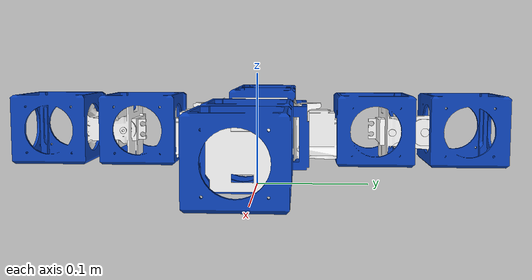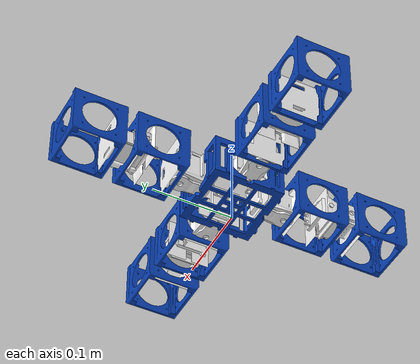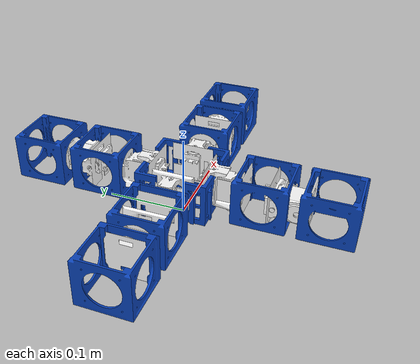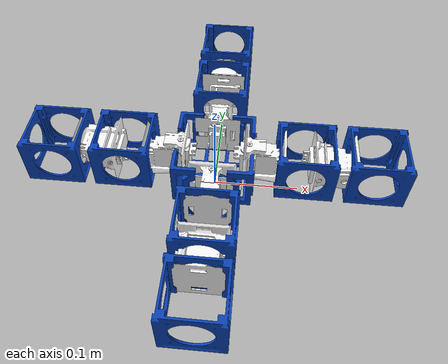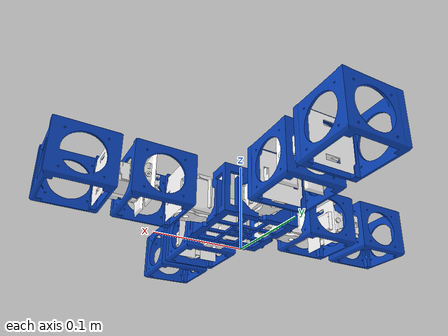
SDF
<?xml version="1.0" encoding="UTF-8"?>
<sdf version="1.5">
  <model name="spider">
    <pose>0.000000e+00 0.000000e+00 5.000000e-02 0.000000e+00 -0.000000e+00 0.000000e+00</pose>
    <link name="link_component_Core__box">
      <pose>0.000000e+00 0.000000e+00 0.000000e+00 0.000000e+00 -0.000000e+00 0.000000e+00</pose>
      <visual name="component_Core__box_visual">
        <pose>0.000000e+00 0.000000e+00 0.000000e+00 0.000000e+00 -0.000000e+00 0.000000e+00</pose>
        <material>
          <ambient>0.04 0.26 0.72 1.0</ambient>
          <diffuse>0.04 0.26 0.72 1.0</diffuse>
          <specular>0.1 0.1 0.1 1.0</specular>
        </material>
        <geometry>
          <mesh>
            <uri>model://rg_robot/meshes/CoreComponent.dae</uri>
          </mesh>
        </geometry>
      </visual>
      <collision name="component_Core__box_collision">
        <pose>0.000000e+00 0.000000e+00 0.000000e+00 0.000000e+00 -0.000000e+00 0.000000e+00</pose>
        <surface>
          <contact>
            <ode>
              <kd>3.333333e+06</kd>
              <kp>9.000000e+04</kp>
            </ode>
          </contact>
          <friction>
            <ode>
              <mu>1.000000e+00</mu>
              <mu2>1.000000e+00</mu2>
              <slip1>1.000000e-02</slip1>
              <slip2>1.000000e-02</slip2>
            </ode>
            <bullet>
              <friction>1.000000e+00</friction>
              <friction2>1.000000e+00</friction2>
            </bullet>
          </friction>
        </surface>
        <geometry>
          <box>
            <size>9.000000e-02 9.000000e-02 4.500000e-02</size>
          </box>
        </geometry>
      </collision>
      <sensor name="Core-imu_sensor" type="imu">
        <pose>0.000000e+00 0.000000e+00 0.000000e+00 0.000000e+00 -0.000000e+00 0.000000e+00</pose>
        <update_rate>8.000000e+00</update_rate>
        <always_on>1</always_on>
      </sensor>
      <visual name="component_Leg00Joint__root_visual">
        <pose>1.665335e-19 -4.575000e-02 4.163336e-20 1.570796e+00 -5.551115e-17 -1.570796e+00</pose>
        <material>
          <ambient>0.98 0.98 0.98 1.0</ambient>
          <diffuse>0.98 0.98 0.98 1.0</diffuse>
          <specular>0.1 0.1 0.1 1.0</specular>
        </material>
        <geometry>
          <box>
            <size>1.500000e-03 3.400000e-02 3.400000e-02</size>
          </box>
        </geometry>
      </visual>
      <collision name="component_Leg00Joint__root_collision">
        <pose>1.665335e-19 -4.575000e-02 4.163336e-20 1.570796e+00 -5.551115e-17 -1.570796e+00</pose>
        <surface>
          <contact>
            <ode>
              <kd>3.333333e+06</kd>
              <kp>9.000000e+04</kp>
            </ode>
          </contact>
          <friction>
            <ode>
              <mu>1.000000e+00</mu>
              <mu2>1.000000e+00</mu2>
              <slip1>1.000000e-02</slip1>
              <slip2>1.000000e-02</slip2>
            </ode>
            <bullet>
              <friction>1.000000e+00</friction>
              <friction2>1.000000e+00</friction2>
            </bullet>
          </friction>
        </surface>
        <geometry>
          <box>
            <size>1.500000e-03 3.400000e-02 3.400000e-02</size>
          </box>
        </geometry>
      </collision>
      <visual name="component_Leg00Joint__frame_frame_visual">
        <pose>2.353673e-18 -5.560000e-02 5.884182e-19 1.570796e+00 -5.551115e-17 -1.570796e+00</pose>
        <material>
          <ambient>0.98 0.98 0.98 1.0</ambient>
          <diffuse>0.98 0.98 0.98 1.0</diffuse>
          <specular>0.1 0.1 0.1 1.0</specular>
        </material>
        <geometry>
          <mesh>
            <uri>model://rg_robot/meshes/ActiveHinge_Frame.dae</uri>
          </mesh>
        </geometry>
      </visual>
      <collision name="component_Leg00Joint__frame_collision">
        <pose>2.353673e-18 -5.560000e-02 5.884182e-19 1.570796e+00 -5.551115e-17 -1.570796e+00</pose>
        <surface>
          <contact>
            <ode>
              <kd>3.333333e+06</kd>
              <kp>9.000000e+04</kp>
            </ode>
          </contact>
          <friction>
            <ode>
              <mu>1.000000e+00</mu>
              <mu2>1.000000e+00</mu2>
              <slip1>1.000000e-02</slip1>
              <slip2>1.000000e-02</slip2>
            </ode>
            <bullet>
              <friction>1.000000e+00</friction>
              <friction2>1.000000e+00</friction2>
            </bullet>
          </friction>
        </surface>
        <geometry>
          <box>
            <size>1.800000e-02 3.400000e-02 1.000000e-02</size>
          </box>
        </geometry>
      </collision>
      <visual name="component_Leg10Joint__root_visual">
        <pose>1.665335e-19 4.575000e-02 -4.163336e-20 1.570796e+00 5.551115e-17 1.570796e+00</pose>
        <material>
          <ambient>0.98 0.98 0.98 1.0</ambient>
          <diffuse>0.98 0.98 0.98 1.0</diffuse>
          <specular>0.1 0.1 0.1 1.0</specular>
        </material>
        <geometry>
          <box>
            <size>1.500000e-03 3.400000e-02 3.400000e-02</size>
          </box>
        </geometry>
      </visual>
      <collision name="component_Leg10Joint__root_collision">
        <pose>1.665335e-19 4.575000e-02 -4.163336e-20 1.570796e+00 5.551115e-17 1.570796e+00</pose>
        <surface>
          <contact>
            <ode>
              <kd>3.333333e+06</kd>
              <kp>9.000000e+04</kp>
            </ode>
          </contact>
          <friction>
            <ode>
              <mu>1.000000e+00</mu>
              <mu2>1.000000e+00</mu2>
              <slip1>1.000000e-02</slip1>
              <slip2>1.000000e-02</slip2>
            </ode>
            <bullet>
              <friction>1.000000e+00</friction>
              <friction2>1.000000e+00</friction2>
            </bullet>
          </friction>
        </surface>
        <geometry>
          <box>
            <size>1.500000e-03 3.400000e-02 3.400000e-02</size>
          </box>
        </geometry>
      </collision>
      <visual name="component_Leg10Joint__frame_frame_visual">
        <pose>2.353673e-18 5.560000e-02 -5.884182e-19 1.570796e+00 5.551115e-17 1.570796e+00</pose>
        <material>
          <ambient>0.98 0.98 0.98 1.0</ambient>
          <diffuse>0.98 0.98 0.98 1.0</diffuse>
          <specular>0.1 0.1 0.1 1.0</specular>
        </material>
        <geometry>
          <mesh>
            <uri>model://rg_robot/meshes/ActiveHinge_Frame.dae</uri>
          </mesh>
        </geometry>
      </visual>
      <collision name="component_Leg10Joint__frame_collision">
        <pose>2.353673e-18 5.560000e-02 -5.884182e-19 1.570796e+00 5.551115e-17 1.570796e+00</pose>
        <surface>
          <contact>
            <ode>
              <kd>3.333333e+06</kd>
              <kp>9.000000e+04</kp>
            </ode>
          </contact>
          <friction>
            <ode>
              <mu>1.000000e+00</mu>
              <mu2>1.000000e+00</mu2>
              <slip1>1.000000e-02</slip1>
              <slip2>1.000000e-02</slip2>
            </ode>
            <bullet>
              <friction>1.000000e+00</friction>
              <friction2>1.000000e+00</friction2>
            </bullet>
          </friction>
        </surface>
        <geometry>
          <box>
            <size>1.800000e-02 3.400000e-02 1.000000e-02</size>
          </box>
        </geometry>
      </collision>
      <visual name="component_Leg20Joint__root_visual">
        <pose>4.575000e-02 0.000000e+00 0.000000e+00 1.570796e+00 -0.000000e+00 0.000000e+00</pose>
        <material>
          <ambient>0.98 0.98 0.98 1.0</ambient>
          <diffuse>0.98 0.98 0.98 1.0</diffuse>
          <specular>0.1 0.1 0.1 1.0</specular>
        </material>
        <geometry>
          <box>
            <size>1.500000e-03 3.400000e-02 3.400000e-02</size>
          </box>
        </geometry>
      </visual>
      <collision name="component_Leg20Joint__root_collision">
        <pose>4.575000e-02 0.000000e+00 0.000000e+00 1.570796e+00 -0.000000e+00 0.000000e+00</pose>
        <surface>
          <contact>
            <ode>
              <kd>3.333333e+06</kd>
              <kp>9.000000e+04</kp>
            </ode>
          </contact>
          <friction>
            <ode>
              <mu>1.000000e+00</mu>
              <mu2>1.000000e+00</mu2>
              <slip1>1.000000e-02</slip1>
              <slip2>1.000000e-02</slip2>
            </ode>
            <bullet>
              <friction>1.000000e+00</friction>
              <friction2>1.000000e+00</friction2>
            </bullet>
          </friction>
        </surface>
        <geometry>
          <box>
            <size>1.500000e-03 3.400000e-02 3.400000e-02</size>
          </box>
        </geometry>
      </collision>
      <visual name="component_Leg20Joint__frame_frame_visual">
        <pose>5.560000e-02 0.000000e+00 0.000000e+00 1.570796e+00 -0.000000e+00 0.000000e+00</pose>
        <material>
          <ambient>0.98 0.98 0.98 1.0</ambient>
          <diffuse>0.98 0.98 0.98 1.0</diffuse>
          <specular>0.1 0.1 0.1 1.0</specular>
        </material>
        <geometry>
          <mesh>
            <uri>model://rg_robot/meshes/ActiveHinge_Frame.dae</uri>
          </mesh>
        </geometry>
      </visual>
      <collision name="component_Leg20Joint__frame_collision">
        <pose>5.560000e-02 0.000000e+00 0.000000e+00 1.570796e+00 -0.000000e+00 0.000000e+00</pose>
        <surface>
          <contact>
            <ode>
              <kd>3.333333e+06</kd>
              <kp>9.000000e+04</kp>
            </ode>
          </contact>
          <friction>
            <ode>
              <mu>1.000000e+00</mu>
              <mu2>1.000000e+00</mu2>
              <slip1>1.000000e-02</slip1>
              <slip2>1.000000e-02</slip2>
            </ode>
            <bullet>
              <friction>1.000000e+00</friction>
              <friction2>1.000000e+00</friction2>
            </bullet>
          </friction>
        </surface>
        <geometry>
          <box>
            <size>1.800000e-02 3.400000e-02 1.000000e-02</size>
          </box>
        </geometry>
      </collision>
      <visual name="component_Leg30Joint__root_visual">
        <pose>-4.575000e-02 0.000000e+00 0.000000e+00 1.570796e+00 -0.000000e+00 3.141593e+00</pose>
        <material>
          <ambient>0.98 0.98 0.98 1.0</ambient>
          <diffuse>0.98 0.98 0.98 1.0</diffuse>
          <specular>0.1 0.1 0.1 1.0</specular>
        </material>
        <geometry>
          <box>
            <size>1.500000e-03 3.400000e-02 3.400000e-02</size>
          </box>
        </geometry>
      </visual>
      <collision name="component_Leg30Joint__root_collision">
        <pose>-4.575000e-02 0.000000e+00 0.000000e+00 1.570796e+00 -0.000000e+00 3.141593e+00</pose>
        <surface>
          <contact>
            <ode>
              <kd>3.333333e+06</kd>
              <kp>9.000000e+04</kp>
            </ode>
          </contact>
          <friction>
            <ode>
              <mu>1.000000e+00</mu>
              <mu2>1.000000e+00</mu2>
              <slip1>1.000000e-02</slip1>
              <slip2>1.000000e-02</slip2>
            </ode>
            <bullet>
              <friction>1.000000e+00</friction>
              <friction2>1.000000e+00</friction2>
            </bullet>
          </friction>
        </surface>
        <geometry>
          <box>
            <size>1.500000e-03 3.400000e-02 3.400000e-02</size>
          </box>
        </geometry>
      </collision>
      <visual name="component_Leg30Joint__frame_frame_visual">
        <pose>-5.560000e-02 0.000000e+00 0.000000e+00 1.570796e+00 -0.000000e+00 3.141593e+00</pose>
        <material>
          <ambient>0.98 0.98 0.98 1.0</ambient>
          <diffuse>0.98 0.98 0.98 1.0</diffuse>
          <specular>0.1 0.1 0.1 1.0</specular>
        </material>
        <geometry>
          <mesh>
            <uri>model://rg_robot/meshes/ActiveHinge_Frame.dae</uri>
          </mesh>
        </geometry>
      </visual>
      <collision name="component_Leg30Joint__frame_collision">
        <pose>-5.560000e-02 0.000000e+00 0.000000e+00 1.570796e+00 -0.000000e+00 3.141593e+00</pose>
        <surface>
          <contact>
            <ode>
              <kd>3.333333e+06</kd>
              <kp>9.000000e+04</kp>
            </ode>
          </contact>
          <friction>
            <ode>
              <mu>1.000000e+00</mu>
              <mu2>1.000000e+00</mu2>
              <slip1>1.000000e-02</slip1>
              <slip2>1.000000e-02</slip2>
            </ode>
            <bullet>
              <friction>1.000000e+00</friction>
              <friction2>1.000000e+00</friction2>
            </bullet>
          </friction>
        </surface>
        <geometry>
          <box>
            <size>1.800000e-02 3.400000e-02 1.000000e-02</size>
          </box>
        </geometry>
      </collision>
      <inertial>
        <mass>1.228000e-01</mass>
        <inertia>
          <ixx>1.172555e-04</ixx>
          <ixy>0.000000e+00</ixy>
          <ixz>-1.763242e-38</ixz>
          <iyy>1.172555e-04</iyy>
          <iyz>4.198228e-22</iyz>
          <izz>1.978165e-04</izz>
        </inertia>
      </inertial>
      <self_collide>True</self_collide>
    </link>
    <link name="link_component_Leg00Joint__servo">
      <pose>1.638200e-17 -9.529797e-02 7.873596e-20 0.000000e+00 -0.000000e+00 0.000000e+00</pose>
      <visual name="component_Leg00Joint__servo_servo_visual">
        <pose>-1.108624e-17 2.644797e-02 1.245205e-18 1.570796e+00 -5.551115e-17 -1.570796e+00</pose>
        <material>
          <ambient>0.98 0.98 0.98 1.0</ambient>
          <diffuse>0.98 0.98 0.98 1.0</diffuse>
          <specular>0.1 0.1 0.1 1.0</specular>
        </material>
        <geometry>
          <mesh>
            <uri>model://rg_robot/meshes/ActiveCardanHinge_Servo_Holder.dae</uri>
          </mesh>
        </geometry>
      </visual>
      <collision name="component_Leg00Joint__servo_collision">
        <pose>-1.108624e-17 2.644797e-02 1.245205e-18 1.570796e+00 -5.551115e-17 -1.570796e+00</pose>
        <surface>
          <contact>
            <ode>
              <kd>3.333333e+06</kd>
              <kp>9.000000e+04</kp>
            </ode>
          </contact>
          <friction>
            <ode>
              <mu>1.000000e+00</mu>
              <mu2>1.000000e+00</mu2>
              <slip1>1.000000e-02</slip1>
              <slip2>1.000000e-02</slip2>
            </ode>
            <bullet>
              <friction>1.000000e+00</friction>
              <friction2>1.000000e+00</friction2>
            </bullet>
          </friction>
        </surface>
        <geometry>
          <box>
            <size>2.450000e-02 3.400000e-02 1.000000e-02</size>
          </box>
        </geometry>
      </collision>
      <collision name="component_Leg00Joint__tail_collision">
        <pose>-8.177453e-18 1.334797e-02 1.972401e-18 1.570796e+00 -5.551115e-17 -1.570796e+00</pose>
        <surface>
          <contact>
            <ode>
              <kd>3.333333e+06</kd>
              <kp>9.000000e+04</kp>
            </ode>
          </contact>
          <friction>
            <ode>
              <mu>1.000000e+00</mu>
              <mu2>1.000000e+00</mu2>
              <slip1>1.000000e-02</slip1>
              <slip2>1.000000e-02</slip2>
            </ode>
            <bullet>
              <friction>1.000000e+00</friction>
              <friction2>1.000000e+00</friction2>
            </bullet>
          </friction>
        </surface>
        <geometry>
          <box>
            <size>1.500000e-03 3.400000e-02 3.400000e-02</size>
          </box>
        </geometry>
      </collision>
      <visual name="component_Leg00__box_visual">
        <pose>6.530768e-18 -7.902035e-03 -3.481570e-18 2.220446e-16 -2.835742e-16 -3.141593e+00</pose>
        <material>
          <ambient>0.04 0.26 0.72 1.0</ambient>
          <diffuse>0.04 0.26 0.72 1.0</diffuse>
          <specular>0.1 0.1 0.1 1.0</specular>
        </material>
        <geometry>
          <mesh>
            <uri>model://rg_robot/meshes/FixedBrick.dae</uri>
          </mesh>
        </geometry>
      </visual>
      <collision name="component_Leg00__box_collision">
        <pose>6.530768e-18 -7.902035e-03 -3.481570e-18 2.220446e-16 -2.835742e-16 -3.141593e+00</pose>
        <surface>
          <contact>
            <ode>
              <kd>3.333333e+06</kd>
              <kp>9.000000e+04</kp>
            </ode>
          </contact>
          <friction>
            <ode>
              <mu>1.000000e+00</mu>
              <mu2>1.000000e+00</mu2>
              <slip1>1.000000e-02</slip1>
              <slip2>1.000000e-02</slip2>
            </ode>
            <bullet>
              <friction>1.000000e+00</friction>
              <friction2>1.000000e+00</friction2>
            </bullet>
          </friction>
        </surface>
        <geometry>
          <box>
            <size>-1.000000e+00 1.000000e+00 3.550000e-02</size>
          </box>
        </geometry>
      </collision>
      <visual name="component_Leg01Joint__root_visual">
        <pose>1.102494e-17 -2.915203e-02 1.142195e-18 -4.098187e-16 -9.580016e-17 -1.570796e+00</pose>
        <material>
          <ambient>0.98 0.98 0.98 1.0</ambient>
          <diffuse>0.98 0.98 0.98 1.0</diffuse>
          <specular>0.1 0.1 0.1 1.0</specular>
        </material>
        <geometry>
          <box>
            <size>1.500000e-03 3.400000e-02 3.400000e-02</size>
          </box>
        </geometry>
      </visual>
      <collision name="component_Leg01Joint__root_collision">
        <pose>1.102494e-17 -2.915203e-02 1.142195e-18 -4.098187e-16 -9.580016e-17 -1.570796e+00</pose>
        <surface>
          <contact>
            <ode>
              <kd>3.333333e+06</kd>
              <kp>9.000000e+04</kp>
            </ode>
          </contact>
          <friction>
            <ode>
              <mu>1.000000e+00</mu>
              <mu2>1.000000e+00</mu2>
              <slip1>1.000000e-02</slip1>
              <slip2>1.000000e-02</slip2>
            </ode>
            <bullet>
              <friction>1.000000e+00</friction>
              <friction2>1.000000e+00</friction2>
            </bullet>
          </friction>
        </surface>
        <geometry>
          <box>
            <size>1.500000e-03 3.400000e-02 3.400000e-02</size>
          </box>
        </geometry>
      </collision>
      <visual name="component_Leg01Joint__frame_frame_visual">
        <pose>1.102494e-17 -3.900203e-02 2.085827e-18 -4.098187e-16 -9.580016e-17 -1.570796e+00</pose>
        <material>
          <ambient>0.98 0.98 0.98 1.0</ambient>
          <diffuse>0.98 0.98 0.98 1.0</diffuse>
          <specular>0.1 0.1 0.1 1.0</specular>
        </material>
        <geometry>
          <mesh>
            <uri>model://rg_robot/meshes/ActiveHinge_Frame.dae</uri>
          </mesh>
        </geometry>
      </visual>
      <collision name="component_Leg01Joint__frame_collision">
        <pose>1.102494e-17 -3.900203e-02 2.085827e-18 -4.098187e-16 -9.580016e-17 -1.570796e+00</pose>
        <surface>
          <contact>
            <ode>
              <kd>3.333333e+06</kd>
              <kp>9.000000e+04</kp>
            </ode>
          </contact>
          <friction>
            <ode>
              <mu>1.000000e+00</mu>
              <mu2>1.000000e+00</mu2>
              <slip1>1.000000e-02</slip1>
              <slip2>1.000000e-02</slip2>
            </ode>
            <bullet>
              <friction>1.000000e+00</friction>
              <friction2>1.000000e+00</friction2>
            </bullet>
          </friction>
        </surface>
        <geometry>
          <box>
            <size>1.800000e-02 3.400000e-02 1.000000e-02</size>
          </box>
        </geometry>
      </collision>
      <inertial>
        <mass>3.440000e-02</mass>
        <inertia>
          <ixx>8.697359e-04</ixx>
          <ixy>6.075862e-21</ixy>
          <ixz>2.401805e-19</ixz>
          <iyy>8.548361e-04</iyy>
          <iyz>1.882799e-19</iyz>
          <izz>1.717978e-03</izz>
        </inertia>
      </inertial>
      <self_collide>True</self_collide>
    </link>
    <link name="link_component_Leg01Joint__servo">
      <pose>2.763933e-17 -1.644229e-01 6.057888e-18 0.000000e+00 -0.000000e+00 0.000000e+00</pose>
      <visual name="component_Leg01Joint__servo_servo_visual">
        <pose>-2.323958e-19 1.687290e-02 -2.623973e-18 -4.098187e-16 -9.580016e-17 -1.570796e+00</pose>
        <material>
          <ambient>0.98 0.98 0.98 1.0</ambient>
          <diffuse>0.98 0.98 0.98 1.0</diffuse>
          <specular>0.1 0.1 0.1 1.0</specular>
        </material>
        <geometry>
          <mesh>
            <uri>model://rg_robot/meshes/ActiveCardanHinge_Servo_Holder.dae</uri>
          </mesh>
        </geometry>
      </visual>
      <collision name="component_Leg01Joint__servo_collision">
        <pose>-2.323958e-19 1.687290e-02 -2.623973e-18 -4.098187e-16 -9.580016e-17 -1.570796e+00</pose>
        <surface>
          <contact>
            <ode>
              <kd>3.333333e+06</kd>
              <kp>9.000000e+04</kp>
            </ode>
          </contact>
          <friction>
            <ode>
              <mu>1.000000e+00</mu>
              <mu2>1.000000e+00</mu2>
              <slip1>1.000000e-02</slip1>
              <slip2>1.000000e-02</slip2>
            </ode>
            <bullet>
              <friction>1.000000e+00</friction>
              <friction2>1.000000e+00</friction2>
            </bullet>
          </friction>
        </surface>
        <geometry>
          <box>
            <size>2.450000e-02 3.400000e-02 1.000000e-02</size>
          </box>
        </geometry>
      </collision>
      <collision name="component_Leg01Joint__tail_collision">
        <pose>-2.323958e-19 3.772901e-03 -1.368991e-18 -4.098187e-16 -9.580016e-17 -1.570796e+00</pose>
        <surface>
          <contact>
            <ode>
              <kd>3.333333e+06</kd>
              <kp>9.000000e+04</kp>
            </ode>
          </contact>
          <friction>
            <ode>
              <mu>1.000000e+00</mu>
              <mu2>1.000000e+00</mu2>
              <slip1>1.000000e-02</slip1>
              <slip2>1.000000e-02</slip2>
            </ode>
            <bullet>
              <friction>1.000000e+00</friction>
              <friction2>1.000000e+00</friction2>
            </bullet>
          </friction>
        </surface>
        <geometry>
          <box>
            <size>1.500000e-03 3.400000e-02 3.400000e-02</size>
          </box>
        </geometry>
      </collision>
      <visual name="component_Leg01__box_visual">
        <pose>3.645424e-19 -1.747710e-02 3.254774e-18 2.220446e-16 -4.098187e-16 -3.141593e+00</pose>
        <material>
          <ambient>0.04 0.26 0.72 1.0</ambient>
          <diffuse>0.04 0.26 0.72 1.0</diffuse>
          <specular>0.1 0.1 0.1 1.0</specular>
        </material>
        <geometry>
          <mesh>
            <uri>model://rg_robot/meshes/FixedBrick.dae</uri>
          </mesh>
        </geometry>
      </visual>
      <collision name="component_Leg01__box_collision">
        <pose>3.645424e-19 -1.747710e-02 3.254774e-18 2.220446e-16 -4.098187e-16 -3.141593e+00</pose>
        <surface>
          <contact>
            <ode>
              <kd>3.333333e+06</kd>
              <kp>9.000000e+04</kp>
            </ode>
          </contact>
          <friction>
            <ode>
              <mu>1.000000e+00</mu>
              <mu2>1.000000e+00</mu2>
              <slip1>1.000000e-02</slip1>
              <slip2>1.000000e-02</slip2>
            </ode>
            <bullet>
              <friction>1.000000e+00</friction>
              <friction2>1.000000e+00</friction2>
            </bullet>
          </friction>
        </surface>
        <geometry>
          <box>
            <size>0.000000e+00 0.000000e+00 3.550000e-02</size>
          </box>
        </geometry>
      </collision>
      <inertial>
        <mass>2.620000e-02</mass>
        <inertia>
          <ixx>8.049522e-06</ixx>
          <ixy>1.064140e-22</ixy>
          <ixz>-1.144265e-22</ixz>
          <iyy>3.361879e-06</iyy>
          <iyz>7.484492e-22</iyz>
          <izz>7.770310e-06</izz>
        </inertia>
      </inertial>
      <self_collide>True</self_collide>
    </link>
    <joint name="joint_link_component_Leg01Joint__servo_link_component_Leg00Joint__servo" type="revolute">
      <pose>1.102494e-17 -4.400203e-02 2.564827e-18 -4.098187e-16 -9.580016e-17 -1.570796e+00</pose>
      <parent>link_component_Leg01Joint__servo</parent>
      <child>link_component_Leg00Joint__servo</child>
      <axis>
        <xyz>0.000000e+00 1.000000e+00 0.000000e+00</xyz>
        <use_parent_model_frame>0</use_parent_model_frame>
        <limit>
          <lower>-7.853982e-01</lower>
          <upper>7.853982e-01</upper>
          <effort>1.765800e-01</effort>
          <velocity>5.235988e+00</velocity>
        </limit>
      </axis>
    </joint>
    <joint name="joint_link_component_Leg00Joint__servo_link_component_Core__box" type="revolute">
      <pose>3.463896e-18 -6.060000e-02 8.659740e-19 1.570796e+00 -5.551115e-17 -1.570796e+00</pose>
      <parent>link_component_Leg00Joint__servo</parent>
      <child>link_component_Core__box</child>
      <axis>
        <xyz>0.000000e+00 1.000000e+00 0.000000e+00</xyz>
        <use_parent_model_frame>0</use_parent_model_frame>
        <limit>
          <lower>-7.853982e-01</lower>
          <upper>7.853982e-01</upper>
          <effort>1.765800e-01</effort>
          <velocity>5.235988e+00</velocity>
        </limit>
      </axis>
    </joint>
    <link name="link_component_Leg10Joint__servo">
      <pose>1.665864e-17 9.529797e-02 7.085631e-18 0.000000e+00 -0.000000e+00 0.000000e+00</pose>
      <visual name="component_Leg10Joint__servo_servo_visual">
        <pose>-1.136287e-17 -2.644797e-02 -8.409571e-18 1.570796e+00 5.551115e-17 1.570796e+00</pose>
        <material>
          <ambient>0.98 0.98 0.98 1.0</ambient>
          <diffuse>0.98 0.98 0.98 1.0</diffuse>
          <specular>0.1 0.1 0.1 1.0</specular>
        </material>
        <geometry>
          <mesh>
            <uri>model://rg_robot/meshes/ActiveCardanHinge_Servo_Holder.dae</uri>
          </mesh>
        </geometry>
      </visual>
      <collision name="component_Leg10Joint__servo_collision">
        <pose>-1.136287e-17 -2.644797e-02 -8.409571e-18 1.570796e+00 5.551115e-17 1.570796e+00</pose>
        <surface>
          <contact>
            <ode>
              <kd>3.333333e+06</kd>
              <kp>9.000000e+04</kp>
            </ode>
          </contact>
          <friction>
            <ode>
              <mu>1.000000e+00</mu>
              <mu2>1.000000e+00</mu2>
              <slip1>1.000000e-02</slip1>
              <slip2>1.000000e-02</slip2>
            </ode>
            <bullet>
              <friction>1.000000e+00</friction>
              <friction2>1.000000e+00</friction2>
            </bullet>
          </friction>
        </surface>
        <geometry>
          <box>
            <size>2.450000e-02 3.400000e-02 1.000000e-02</size>
          </box>
        </geometry>
      </collision>
      <collision name="component_Leg10Joint__tail_collision">
        <pose>-8.454090e-18 -1.334797e-02 -9.136768e-18 1.570796e+00 5.551115e-17 1.570796e+00</pose>
        <surface>
          <contact>
            <ode>
              <kd>3.333333e+06</kd>
              <kp>9.000000e+04</kp>
            </ode>
          </contact>
          <friction>
            <ode>
              <mu>1.000000e+00</mu>
              <mu2>1.000000e+00</mu2>
              <slip1>1.000000e-02</slip1>
              <slip2>1.000000e-02</slip2>
            </ode>
            <bullet>
              <friction>1.000000e+00</friction>
              <friction2>1.000000e+00</friction2>
            </bullet>
          </friction>
        </surface>
        <geometry>
          <box>
            <size>1.500000e-03 3.400000e-02 3.400000e-02</size>
          </box>
        </geometry>
      </collision>
      <visual name="component_Leg10__box_visual">
        <pose>6.311876e-18 7.902035e-03 5.305540e-18 2.164109e-16 -2.220446e-16 -2.220446e-16</pose>
        <material>
          <ambient>0.04 0.26 0.72 1.0</ambient>
          <diffuse>0.04 0.26 0.72 1.0</diffuse>
          <specular>0.1 0.1 0.1 1.0</specular>
        </material>
        <geometry>
          <mesh>
            <uri>model://rg_robot/meshes/FixedBrick.dae</uri>
          </mesh>
        </geometry>
      </visual>
      <collision name="component_Leg10__box_collision">
        <pose>6.311876e-18 7.902035e-03 5.305540e-18 2.164109e-16 -2.220446e-16 -2.220446e-16</pose>
        <surface>
          <contact>
            <ode>
              <kd>3.333333e+06</kd>
              <kp>9.000000e+04</kp>
            </ode>
          </contact>
          <friction>
            <ode>
              <mu>1.000000e+00</mu>
              <mu2>1.000000e+00</mu2>
              <slip1>1.000000e-02</slip1>
              <slip2>1.000000e-02</slip2>
            </ode>
            <bullet>
              <friction>1.000000e+00</friction>
              <friction2>1.000000e+00</friction2>
            </bullet>
          </friction>
        </surface>
        <geometry>
          <box>
            <size>1.000000e+00 1.000000e+00 3.550000e-02</size>
          </box>
        </geometry>
      </collision>
      <visual name="component_Leg11Joint__root_visual">
        <pose>1.119686e-17 2.915203e-02 9.977477e-18 -3.140185e-16 -3.140185e-16 1.570796e+00</pose>
        <material>
          <ambient>0.98 0.98 0.98 1.0</ambient>
          <diffuse>0.98 0.98 0.98 1.0</diffuse>
          <specular>0.1 0.1 0.1 1.0</specular>
        </material>
        <geometry>
          <box>
            <size>1.500000e-03 3.400000e-02 3.400000e-02</size>
          </box>
        </geometry>
      </visual>
      <collision name="component_Leg11Joint__root_collision">
        <pose>1.119686e-17 2.915203e-02 9.977477e-18 -3.140185e-16 -3.140185e-16 1.570796e+00</pose>
        <surface>
          <contact>
            <ode>
              <kd>3.333333e+06</kd>
              <kp>9.000000e+04</kp>
            </ode>
          </contact>
          <friction>
            <ode>
              <mu>1.000000e+00</mu>
              <mu2>1.000000e+00</mu2>
              <slip1>1.000000e-02</slip1>
              <slip2>1.000000e-02</slip2>
            </ode>
            <bullet>
              <friction>1.000000e+00</friction>
              <friction2>1.000000e+00</friction2>
            </bullet>
          </friction>
        </surface>
        <geometry>
          <box>
            <size>1.500000e-03 3.400000e-02 3.400000e-02</size>
          </box>
        </geometry>
      </collision>
      <visual name="component_Leg11Joint__frame_frame_visual">
        <pose>1.557114e-17 3.900203e-02 1.307056e-17 -3.140185e-16 -3.140185e-16 1.570796e+00</pose>
        <material>
          <ambient>0.98 0.98 0.98 1.0</ambient>
          <diffuse>0.98 0.98 0.98 1.0</diffuse>
          <specular>0.1 0.1 0.1 1.0</specular>
        </material>
        <geometry>
          <mesh>
            <uri>model://rg_robot/meshes/ActiveHinge_Frame.dae</uri>
          </mesh>
        </geometry>
      </visual>
      <collision name="component_Leg11Joint__frame_collision">
        <pose>1.557114e-17 3.900203e-02 1.307056e-17 -3.140185e-16 -3.140185e-16 1.570796e+00</pose>
        <surface>
          <contact>
            <ode>
              <kd>3.333333e+06</kd>
              <kp>9.000000e+04</kp>
            </ode>
          </contact>
          <friction>
            <ode>
              <mu>1.000000e+00</mu>
              <mu2>1.000000e+00</mu2>
              <slip1>1.000000e-02</slip1>
              <slip2>1.000000e-02</slip2>
            </ode>
            <bullet>
              <friction>1.000000e+00</friction>
              <friction2>1.000000e+00</friction2>
            </bullet>
          </friction>
        </surface>
        <geometry>
          <box>
            <size>1.800000e-02 3.400000e-02 1.000000e-02</size>
          </box>
        </geometry>
      </collision>
      <inertial>
        <mass>3.440000e-02</mass>
        <inertia>
          <ixx>8.697359e-04</ixx>
          <ixy>-6.061942e-21</ixy>
          <ixz>-1.879361e-19</ixz>
          <iyy>8.548361e-04</iyy>
          <iyz>-1.891712e-19</iyz>
          <izz>1.717978e-03</izz>
        </inertia>
      </inertial>
      <self_collide>True</self_collide>
    </link>
    <link name="link_component_Leg11Joint__servo">
      <pose>4.582202e-17 1.644229e-01 2.961534e-17 0.000000e+00 -0.000000e+00 0.000000e+00</pose>
      <visual name="component_Leg11Joint__servo_servo_visual">
        <pose>-7.708067e-18 -1.687290e-02 -5.298403e-18 -3.140185e-16 -3.140185e-16 1.570796e+00</pose>
        <material>
          <ambient>0.98 0.98 0.98 1.0</ambient>
          <diffuse>0.98 0.98 0.98 1.0</diffuse>
          <specular>0.1 0.1 0.1 1.0</specular>
        </material>
        <geometry>
          <mesh>
            <uri>model://rg_robot/meshes/ActiveCardanHinge_Servo_Holder.dae</uri>
          </mesh>
        </geometry>
      </visual>
      <collision name="component_Leg11Joint__servo_collision">
        <pose>-7.708067e-18 -1.687290e-02 -5.298403e-18 -3.140185e-16 -3.140185e-16 1.570796e+00</pose>
        <surface>
          <contact>
            <ode>
              <kd>3.333333e+06</kd>
              <kp>9.000000e+04</kp>
            </ode>
          </contact>
          <friction>
            <ode>
              <mu>1.000000e+00</mu>
              <mu2>1.000000e+00</mu2>
              <slip1>1.000000e-02</slip1>
              <slip2>1.000000e-02</slip2>
            </ode>
            <bullet>
              <friction>1.000000e+00</friction>
              <friction2>1.000000e+00</friction2>
            </bullet>
          </friction>
        </surface>
        <geometry>
          <box>
            <size>2.450000e-02 3.400000e-02 1.000000e-02</size>
          </box>
        </geometry>
      </collision>
      <collision name="component_Leg11Joint__tail_collision">
        <pose>-1.890499e-18 -3.772901e-03 -1.184761e-18 -3.140185e-16 -3.140185e-16 1.570796e+00</pose>
        <surface>
          <contact>
            <ode>
              <kd>3.333333e+06</kd>
              <kp>9.000000e+04</kp>
            </ode>
          </contact>
          <friction>
            <ode>
              <mu>1.000000e+00</mu>
              <mu2>1.000000e+00</mu2>
              <slip1>1.000000e-02</slip1>
              <slip2>1.000000e-02</slip2>
            </ode>
            <bullet>
              <friction>1.000000e+00</friction>
              <friction2>1.000000e+00</friction2>
            </bullet>
          </friction>
        </surface>
        <geometry>
          <box>
            <size>1.500000e-03 3.400000e-02 3.400000e-02</size>
          </box>
        </geometry>
      </collision>
      <visual name="component_Leg11__box_visual">
        <pose>8.098637e-18 1.747710e-02 5.488132e-18 3.140185e-16 -4.440892e-16 -4.710277e-16</pose>
        <material>
          <ambient>0.04 0.26 0.72 1.0</ambient>
          <diffuse>0.04 0.26 0.72 1.0</diffuse>
          <specular>0.1 0.1 0.1 1.0</specular>
        </material>
        <geometry>
          <mesh>
            <uri>model://rg_robot/meshes/FixedBrick.dae</uri>
          </mesh>
        </geometry>
      </visual>
      <collision name="component_Leg11__box_collision">
        <pose>8.098637e-18 1.747710e-02 5.488132e-18 3.140185e-16 -4.440892e-16 -4.710277e-16</pose>
        <surface>
          <contact>
            <ode>
              <kd>3.333333e+06</kd>
              <kp>9.000000e+04</kp>
            </ode>
          </contact>
          <friction>
            <ode>
              <mu>1.000000e+00</mu>
              <mu2>1.000000e+00</mu2>
              <slip1>1.000000e-02</slip1>
              <slip2>1.000000e-02</slip2>
            </ode>
            <bullet>
              <friction>1.000000e+00</friction>
              <friction2>1.000000e+00</friction2>
            </bullet>
          </friction>
        </surface>
        <geometry>
          <box>
            <size>2.000000e+00 0.000000e+00 3.550000e-02</size>
          </box>
        </geometry>
      </collision>
      <inertial>
        <mass>2.620000e-02</mass>
        <inertia>
          <ixx>8.049522e-06</ixx>
          <ixy>1.599314e-18</ixy>
          <ixz>-1.509676e-18</ixz>
          <iyy>3.403362e-03</iyy>
          <iyz>-1.384329e-21</iyz>
          <izz>3.407770e-03</izz>
        </inertia>
      </inertial>
      <self_collide>True</self_collide>
    </link>
    <joint name="joint_link_component_Leg11Joint__servo_link_component_Leg10Joint__servo" type="revolute">
      <pose>1.779158e-17 4.400203e-02 1.464065e-17 -3.140185e-16 -3.140185e-16 1.570796e+00</pose>
      <parent>link_component_Leg11Joint__servo</parent>
      <child>link_component_Leg10Joint__servo</child>
      <axis>
        <xyz>0.000000e+00 1.000000e+00 0.000000e+00</xyz>
        <use_parent_model_frame>0</use_parent_model_frame>
        <limit>
          <lower>-7.853982e-01</lower>
          <upper>7.853982e-01</upper>
          <effort>1.765800e-01</effort>
          <velocity>5.235988e+00</velocity>
        </limit>
      </axis>
    </joint>
    <joint name="joint_link_component_Leg10Joint__servo_link_component_Core__box" type="revolute">
      <pose>3.463896e-18 6.060000e-02 -8.659740e-19 1.570796e+00 5.551115e-17 1.570796e+00</pose>
      <parent>link_component_Leg10Joint__servo</parent>
      <child>link_component_Core__box</child>
      <axis>
        <xyz>0.000000e+00 1.000000e+00 0.000000e+00</xyz>
        <use_parent_model_frame>0</use_parent_model_frame>
        <limit>
          <lower>-7.853982e-01</lower>
          <upper>7.853982e-01</upper>
          <effort>1.765800e-01</effort>
          <velocity>5.235988e+00</velocity>
        </limit>
      </axis>
    </joint>
    <link name="link_component_Leg20Joint__servo">
      <pose>9.529797e-02 0.000000e+00 0.000000e+00 0.000000e+00 -0.000000e+00 0.000000e+00</pose>
      <visual name="component_Leg20Joint__servo_servo_visual">
        <pose>-2.644797e-02 0.000000e+00 0.000000e+00 1.570796e+00 -0.000000e+00 0.000000e+00</pose>
        <material>
          <ambient>0.98 0.98 0.98 1.0</ambient>
          <diffuse>0.98 0.98 0.98 1.0</diffuse>
          <specular>0.1 0.1 0.1 1.0</specular>
        </material>
        <geometry>
          <mesh>
            <uri>model://rg_robot/meshes/ActiveCardanHinge_Servo_Holder.dae</uri>
          </mesh>
        </geometry>
      </visual>
      <collision name="component_Leg20Joint__servo_collision">
        <pose>-2.644797e-02 0.000000e+00 0.000000e+00 1.570796e+00 -0.000000e+00 0.000000e+00</pose>
        <surface>
          <contact>
            <ode>
              <kd>3.333333e+06</kd>
              <kp>9.000000e+04</kp>
            </ode>
          </contact>
          <friction>
            <ode>
              <mu>1.000000e+00</mu>
              <mu2>1.000000e+00</mu2>
              <slip1>1.000000e-02</slip1>
              <slip2>1.000000e-02</slip2>
            </ode>
            <bullet>
              <friction>1.000000e+00</friction>
              <friction2>1.000000e+00</friction2>
            </bullet>
          </friction>
        </surface>
        <geometry>
          <box>
            <size>2.450000e-02 3.400000e-02 1.000000e-02</size>
          </box>
        </geometry>
      </collision>
      <collision name="component_Leg20Joint__tail_collision">
        <pose>-1.334797e-02 0.000000e+00 0.000000e+00 1.570796e+00 -0.000000e+00 0.000000e+00</pose>
        <surface>
          <contact>
            <ode>
              <kd>3.333333e+06</kd>
              <kp>9.000000e+04</kp>
            </ode>
          </contact>
          <friction>
            <ode>
              <mu>1.000000e+00</mu>
              <mu2>1.000000e+00</mu2>
              <slip1>1.000000e-02</slip1>
              <slip2>1.000000e-02</slip2>
            </ode>
            <bullet>
              <friction>1.000000e+00</friction>
              <friction2>1.000000e+00</friction2>
            </bullet>
          </friction>
        </surface>
        <geometry>
          <box>
            <size>1.500000e-03 3.400000e-02 3.400000e-02</size>
          </box>
        </geometry>
      </collision>
      <visual name="component_Leg20__box_visual">
        <pose>7.902035e-03 0.000000e+00 0.000000e+00 0.000000e+00 0.000000e+00 -1.570796e+00</pose>
        <material>
          <ambient>0.04 0.26 0.72 1.0</ambient>
          <diffuse>0.04 0.26 0.72 1.0</diffuse>
          <specular>0.1 0.1 0.1 1.0</specular>
        </material>
        <geometry>
          <mesh>
            <uri>model://rg_robot/meshes/FixedBrick.dae</uri>
          </mesh>
        </geometry>
      </visual>
      <collision name="component_Leg20__box_collision">
        <pose>7.902035e-03 0.000000e+00 0.000000e+00 0.000000e+00 0.000000e+00 -1.570796e+00</pose>
        <surface>
          <contact>
            <ode>
              <kd>3.333333e+06</kd>
              <kp>9.000000e+04</kp>
            </ode>
          </contact>
          <friction>
            <ode>
              <mu>1.000000e+00</mu>
              <mu2>1.000000e+00</mu2>
              <slip1>1.000000e-02</slip1>
              <slip2>1.000000e-02</slip2>
            </ode>
            <bullet>
              <friction>1.000000e+00</friction>
              <friction2>1.000000e+00</friction2>
            </bullet>
          </friction>
        </surface>
        <geometry>
          <box>
            <size>0.000000e+00 0.000000e+00 3.550000e-02</size>
          </box>
        </geometry>
      </collision>
      <visual name="component_Leg21Joint__root_visual">
        <pose>2.915203e-02 0.000000e+00 0.000000e+00 0.000000e+00 -0.000000e+00 0.000000e+00</pose>
        <material>
          <ambient>0.98 0.98 0.98 1.0</ambient>
          <diffuse>0.98 0.98 0.98 1.0</diffuse>
          <specular>0.1 0.1 0.1 1.0</specular>
        </material>
        <geometry>
          <box>
            <size>1.500000e-03 3.400000e-02 3.400000e-02</size>
          </box>
        </geometry>
      </visual>
      <collision name="component_Leg21Joint__root_collision">
        <pose>2.915203e-02 0.000000e+00 0.000000e+00 0.000000e+00 -0.000000e+00 0.000000e+00</pose>
        <surface>
          <contact>
            <ode>
              <kd>3.333333e+06</kd>
              <kp>9.000000e+04</kp>
            </ode>
          </contact>
          <friction>
            <ode>
              <mu>1.000000e+00</mu>
              <mu2>1.000000e+00</mu2>
              <slip1>1.000000e-02</slip1>
              <slip2>1.000000e-02</slip2>
            </ode>
            <bullet>
              <friction>1.000000e+00</friction>
              <friction2>1.000000e+00</friction2>
            </bullet>
          </friction>
        </surface>
        <geometry>
          <box>
            <size>1.500000e-03 3.400000e-02 3.400000e-02</size>
          </box>
        </geometry>
      </collision>
      <visual name="component_Leg21Joint__frame_frame_visual">
        <pose>3.900203e-02 0.000000e+00 0.000000e+00 0.000000e+00 -0.000000e+00 0.000000e+00</pose>
        <material>
          <ambient>0.98 0.98 0.98 1.0</ambient>
          <diffuse>0.98 0.98 0.98 1.0</diffuse>
          <specular>0.1 0.1 0.1 1.0</specular>
        </material>
        <geometry>
          <mesh>
            <uri>model://rg_robot/meshes/ActiveHinge_Frame.dae</uri>
          </mesh>
        </geometry>
      </visual>
      <collision name="component_Leg21Joint__frame_collision">
        <pose>3.900203e-02 0.000000e+00 0.000000e+00 0.000000e+00 -0.000000e+00 0.000000e+00</pose>
        <surface>
          <contact>
            <ode>
              <kd>3.333333e+06</kd>
              <kp>9.000000e+04</kp>
            </ode>
          </contact>
          <friction>
            <ode>
              <mu>1.000000e+00</mu>
              <mu2>1.000000e+00</mu2>
              <slip1>1.000000e-02</slip1>
              <slip2>1.000000e-02</slip2>
            </ode>
            <bullet>
              <friction>1.000000e+00</friction>
              <friction2>1.000000e+00</friction2>
            </bullet>
          </friction>
        </surface>
        <geometry>
          <box>
            <size>1.800000e-02 3.400000e-02 1.000000e-02</size>
          </box>
        </geometry>
      </collision>
      <inertial>
        <mass>3.440000e-02</mass>
        <inertia>
          <ixx>4.836146e-06</ixx>
          <ixy>0.000000e+00</ixy>
          <ixz>0.000000e+00</ixz>
          <iyy>1.973591e-05</iyy>
          <iyz>0.000000e+00</iyz>
          <izz>1.797830e-05</izz>
        </inertia>
      </inertial>
      <self_collide>True</self_collide>
    </link>
    <link name="link_component_Leg21Joint__servo">
      <pose>1.644229e-01 0.000000e+00 0.000000e+00 0.000000e+00 -0.000000e+00 0.000000e+00</pose>
      <visual name="component_Leg21Joint__servo_servo_visual">
        <pose>-1.687290e-02 0.000000e+00 0.000000e+00 0.000000e+00 -0.000000e+00 0.000000e+00</pose>
        <material>
          <ambient>0.98 0.98 0.98 1.0</ambient>
          <diffuse>0.98 0.98 0.98 1.0</diffuse>
          <specular>0.1 0.1 0.1 1.0</specular>
        </material>
        <geometry>
          <mesh>
            <uri>model://rg_robot/meshes/ActiveCardanHinge_Servo_Holder.dae</uri>
          </mesh>
        </geometry>
      </visual>
      <collision name="component_Leg21Joint__servo_collision">
        <pose>-1.687290e-02 0.000000e+00 0.000000e+00 0.000000e+00 -0.000000e+00 0.000000e+00</pose>
        <surface>
          <contact>
            <ode>
              <kd>3.333333e+06</kd>
              <kp>9.000000e+04</kp>
            </ode>
          </contact>
          <friction>
            <ode>
              <mu>1.000000e+00</mu>
              <mu2>1.000000e+00</mu2>
              <slip1>1.000000e-02</slip1>
              <slip2>1.000000e-02</slip2>
            </ode>
            <bullet>
              <friction>1.000000e+00</friction>
              <friction2>1.000000e+00</friction2>
            </bullet>
          </friction>
        </surface>
        <geometry>
          <box>
            <size>2.450000e-02 3.400000e-02 1.000000e-02</size>
          </box>
        </geometry>
      </collision>
      <collision name="component_Leg21Joint__tail_collision">
        <pose>-3.772901e-03 0.000000e+00 0.000000e+00 0.000000e+00 -0.000000e+00 0.000000e+00</pose>
        <surface>
          <contact>
            <ode>
              <kd>3.333333e+06</kd>
              <kp>9.000000e+04</kp>
            </ode>
          </contact>
          <friction>
            <ode>
              <mu>1.000000e+00</mu>
              <mu2>1.000000e+00</mu2>
              <slip1>1.000000e-02</slip1>
              <slip2>1.000000e-02</slip2>
            </ode>
            <bullet>
              <friction>1.000000e+00</friction>
              <friction2>1.000000e+00</friction2>
            </bullet>
          </friction>
        </surface>
        <geometry>
          <box>
            <size>1.500000e-03 3.400000e-02 3.400000e-02</size>
          </box>
        </geometry>
      </collision>
      <visual name="component_Leg21__box_visual">
        <pose>1.747710e-02 0.000000e+00 0.000000e+00 0.000000e+00 0.000000e+00 -1.570796e+00</pose>
        <material>
          <ambient>0.04 0.26 0.72 1.0</ambient>
          <diffuse>0.04 0.26 0.72 1.0</diffuse>
          <specular>0.1 0.1 0.1 1.0</specular>
        </material>
        <geometry>
          <mesh>
            <uri>model://rg_robot/meshes/FixedBrick.dae</uri>
          </mesh>
        </geometry>
      </visual>
      <collision name="component_Leg21__box_collision">
        <pose>1.747710e-02 0.000000e+00 0.000000e+00 0.000000e+00 0.000000e+00 -1.570796e+00</pose>
        <surface>
          <contact>
            <ode>
              <kd>3.333333e+06</kd>
              <kp>9.000000e+04</kp>
            </ode>
          </contact>
          <friction>
            <ode>
              <mu>1.000000e+00</mu>
              <mu2>1.000000e+00</mu2>
              <slip1>1.000000e-02</slip1>
              <slip2>1.000000e-02</slip2>
            </ode>
            <bullet>
              <friction>1.000000e+00</friction>
              <friction2>1.000000e+00</friction2>
            </bullet>
          </friction>
        </surface>
        <geometry>
          <box>
            <size>1.000000e+00 -1.000000e+00 3.550000e-02</size>
          </box>
        </geometry>
      </collision>
      <inertial>
        <mass>2.620000e-02</mass>
        <inertia>
          <ixx>8.533619e-04</ixx>
          <ixy>0.000000e+00</ixy>
          <ixz>0.000000e+00</ixz>
          <iyy>8.580495e-04</iyy>
          <iyz>0.000000e+00</iyz>
          <izz>1.707770e-03</izz>
        </inertia>
      </inertial>
      <self_collide>True</self_collide>
    </link>
    <joint name="joint_link_component_Leg21Joint__servo_link_component_Leg20Joint__servo" type="revolute">
      <pose>4.400203e-02 0.000000e+00 0.000000e+00 0.000000e+00 -0.000000e+00 0.000000e+00</pose>
      <parent>link_component_Leg21Joint__servo</parent>
      <child>link_component_Leg20Joint__servo</child>
      <axis>
        <xyz>0.000000e+00 1.000000e+00 0.000000e+00</xyz>
        <use_parent_model_frame>0</use_parent_model_frame>
        <limit>
          <lower>-7.853982e-01</lower>
          <upper>7.853982e-01</upper>
          <effort>1.765800e-01</effort>
          <velocity>5.235988e+00</velocity>
        </limit>
      </axis>
    </joint>
    <joint name="joint_link_component_Leg20Joint__servo_link_component_Core__box" type="revolute">
      <pose>6.060000e-02 0.000000e+00 0.000000e+00 1.570796e+00 -0.000000e+00 0.000000e+00</pose>
      <parent>link_component_Leg20Joint__servo</parent>
      <child>link_component_Core__box</child>
      <axis>
        <xyz>0.000000e+00 1.000000e+00 0.000000e+00</xyz>
        <use_parent_model_frame>0</use_parent_model_frame>
        <limit>
          <lower>-7.853982e-01</lower>
          <upper>7.853982e-01</upper>
          <effort>1.765800e-01</effort>
          <velocity>5.235988e+00</velocity>
        </limit>
      </axis>
    </joint>
    <link name="link_component_Leg30Joint__servo">
      <pose>-9.529797e-02 0.000000e+00 0.000000e+00 0.000000e+00 -0.000000e+00 0.000000e+00</pose>
      <visual name="component_Leg30Joint__servo_servo_visual">
        <pose>2.644797e-02 0.000000e+00 0.000000e+00 1.570796e+00 -0.000000e+00 3.141593e+00</pose>
        <material>
          <ambient>0.98 0.98 0.98 1.0</ambient>
          <diffuse>0.98 0.98 0.98 1.0</diffuse>
          <specular>0.1 0.1 0.1 1.0</specular>
        </material>
        <geometry>
          <mesh>
            <uri>model://rg_robot/meshes/ActiveCardanHinge_Servo_Holder.dae</uri>
          </mesh>
        </geometry>
      </visual>
      <collision name="component_Leg30Joint__servo_collision">
        <pose>2.644797e-02 0.000000e+00 0.000000e+00 1.570796e+00 -0.000000e+00 3.141593e+00</pose>
        <surface>
          <contact>
            <ode>
              <kd>3.333333e+06</kd>
              <kp>9.000000e+04</kp>
            </ode>
          </contact>
          <friction>
            <ode>
              <mu>1.000000e+00</mu>
              <mu2>1.000000e+00</mu2>
              <slip1>1.000000e-02</slip1>
              <slip2>1.000000e-02</slip2>
            </ode>
            <bullet>
              <friction>1.000000e+00</friction>
              <friction2>1.000000e+00</friction2>
            </bullet>
          </friction>
        </surface>
        <geometry>
          <box>
            <size>2.450000e-02 3.400000e-02 1.000000e-02</size>
          </box>
        </geometry>
      </collision>
      <collision name="component_Leg30Joint__tail_collision">
        <pose>1.334797e-02 0.000000e+00 0.000000e+00 1.570796e+00 -0.000000e+00 3.141593e+00</pose>
        <surface>
          <contact>
            <ode>
              <kd>3.333333e+06</kd>
              <kp>9.000000e+04</kp>
            </ode>
          </contact>
          <friction>
            <ode>
              <mu>1.000000e+00</mu>
              <mu2>1.000000e+00</mu2>
              <slip1>1.000000e-02</slip1>
              <slip2>1.000000e-02</slip2>
            </ode>
            <bullet>
              <friction>1.000000e+00</friction>
              <friction2>1.000000e+00</friction2>
            </bullet>
          </friction>
        </surface>
        <geometry>
          <box>
            <size>1.500000e-03 3.400000e-02 3.400000e-02</size>
          </box>
        </geometry>
      </collision>
      <visual name="component_Leg30__box_visual">
        <pose>-7.902035e-03 0.000000e+00 0.000000e+00 0.000000e+00 -0.000000e+00 1.570796e+00</pose>
        <material>
          <ambient>0.04 0.26 0.72 1.0</ambient>
          <diffuse>0.04 0.26 0.72 1.0</diffuse>
          <specular>0.1 0.1 0.1 1.0</specular>
        </material>
        <geometry>
          <mesh>
            <uri>model://rg_robot/meshes/FixedBrick.dae</uri>
          </mesh>
        </geometry>
      </visual>
      <collision name="component_Leg30__box_collision">
        <pose>-7.902035e-03 0.000000e+00 0.000000e+00 0.000000e+00 -0.000000e+00 1.570796e+00</pose>
        <surface>
          <contact>
            <ode>
              <kd>3.333333e+06</kd>
              <kp>9.000000e+04</kp>
            </ode>
          </contact>
          <friction>
            <ode>
              <mu>1.000000e+00</mu>
              <mu2>1.000000e+00</mu2>
              <slip1>1.000000e-02</slip1>
              <slip2>1.000000e-02</slip2>
            </ode>
            <bullet>
              <friction>1.000000e+00</friction>
              <friction2>1.000000e+00</friction2>
            </bullet>
          </friction>
        </surface>
        <geometry>
          <box>
            <size>0.000000e+00 2.000000e+00 3.550000e-02</size>
          </box>
        </geometry>
      </collision>
      <visual name="component_Leg31Joint__root_visual">
        <pose>-2.915203e-02 0.000000e+00 0.000000e+00 0.000000e+00 -0.000000e+00 3.141593e+00</pose>
        <material>
          <ambient>0.98 0.98 0.98 1.0</ambient>
          <diffuse>0.98 0.98 0.98 1.0</diffuse>
          <specular>0.1 0.1 0.1 1.0</specular>
        </material>
        <geometry>
          <box>
            <size>1.500000e-03 3.400000e-02 3.400000e-02</size>
          </box>
        </geometry>
      </visual>
      <collision name="component_Leg31Joint__root_collision">
        <pose>-2.915203e-02 0.000000e+00 0.000000e+00 0.000000e+00 -0.000000e+00 3.141593e+00</pose>
        <surface>
          <contact>
            <ode>
              <kd>3.333333e+06</kd>
              <kp>9.000000e+04</kp>
            </ode>
          </contact>
          <friction>
            <ode>
              <mu>1.000000e+00</mu>
              <mu2>1.000000e+00</mu2>
              <slip1>1.000000e-02</slip1>
              <slip2>1.000000e-02</slip2>
            </ode>
            <bullet>
              <friction>1.000000e+00</friction>
              <friction2>1.000000e+00</friction2>
            </bullet>
          </friction>
        </surface>
        <geometry>
          <box>
            <size>1.500000e-03 3.400000e-02 3.400000e-02</size>
          </box>
        </geometry>
      </collision>
      <visual name="component_Leg31Joint__frame_frame_visual">
        <pose>-3.900203e-02 0.000000e+00 0.000000e+00 0.000000e+00 -0.000000e+00 3.141593e+00</pose>
        <material>
          <ambient>0.98 0.98 0.98 1.0</ambient>
          <diffuse>0.98 0.98 0.98 1.0</diffuse>
          <specular>0.1 0.1 0.1 1.0</specular>
        </material>
        <geometry>
          <mesh>
            <uri>model://rg_robot/meshes/ActiveHinge_Frame.dae</uri>
          </mesh>
        </geometry>
      </visual>
      <collision name="component_Leg31Joint__frame_collision">
        <pose>-3.900203e-02 0.000000e+00 0.000000e+00 0.000000e+00 -0.000000e+00 3.141593e+00</pose>
        <surface>
          <contact>
            <ode>
              <kd>3.333333e+06</kd>
              <kp>9.000000e+04</kp>
            </ode>
          </contact>
          <friction>
            <ode>
              <mu>1.000000e+00</mu>
              <mu2>1.000000e+00</mu2>
              <slip1>1.000000e-02</slip1>
              <slip2>1.000000e-02</slip2>
            </ode>
            <bullet>
              <friction>1.000000e+00</friction>
              <friction2>1.000000e+00</friction2>
            </bullet>
          </friction>
        </surface>
        <geometry>
          <box>
            <size>1.800000e-02 3.400000e-02 1.000000e-02</size>
          </box>
        </geometry>
      </collision>
      <inertial>
        <mass>3.440000e-02</mass>
        <inertia>
          <ixx>4.836146e-06</ixx>
          <ixy>0.000000e+00</ixy>
          <ixz>0.000000e+00</ixz>
          <iyy>3.419736e-03</iyy>
          <iyz>0.000000e+00</iyz>
          <izz>3.417978e-03</izz>
        </inertia>
      </inertial>
      <self_collide>True</self_collide>
    </link>
    <link name="link_component_Leg31Joint__servo">
      <pose>-1.644229e-01 0.000000e+00 0.000000e+00 0.000000e+00 -0.000000e+00 0.000000e+00</pose>
      <visual name="component_Leg31Joint__servo_servo_visual">
        <pose>1.687290e-02 0.000000e+00 0.000000e+00 0.000000e+00 -0.000000e+00 3.141593e+00</pose>
        <material>
          <ambient>0.98 0.98 0.98 1.0</ambient>
          <diffuse>0.98 0.98 0.98 1.0</diffuse>
          <specular>0.1 0.1 0.1 1.0</specular>
        </material>
        <geometry>
          <mesh>
            <uri>model://rg_robot/meshes/ActiveCardanHinge_Servo_Holder.dae</uri>
          </mesh>
        </geometry>
      </visual>
      <collision name="component_Leg31Joint__servo_collision">
        <pose>1.687290e-02 0.000000e+00 0.000000e+00 0.000000e+00 -0.000000e+00 3.141593e+00</pose>
        <surface>
          <contact>
            <ode>
              <kd>3.333333e+06</kd>
              <kp>9.000000e+04</kp>
            </ode>
          </contact>
          <friction>
            <ode>
              <mu>1.000000e+00</mu>
              <mu2>1.000000e+00</mu2>
              <slip1>1.000000e-02</slip1>
              <slip2>1.000000e-02</slip2>
            </ode>
            <bullet>
              <friction>1.000000e+00</friction>
              <friction2>1.000000e+00</friction2>
            </bullet>
          </friction>
        </surface>
        <geometry>
          <box>
            <size>2.450000e-02 3.400000e-02 1.000000e-02</size>
          </box>
        </geometry>
      </collision>
      <collision name="component_Leg31Joint__tail_collision">
        <pose>3.772901e-03 0.000000e+00 0.000000e+00 0.000000e+00 -0.000000e+00 3.141593e+00</pose>
        <surface>
          <contact>
            <ode>
              <kd>3.333333e+06</kd>
              <kp>9.000000e+04</kp>
            </ode>
          </contact>
          <friction>
            <ode>
              <mu>1.000000e+00</mu>
              <mu2>1.000000e+00</mu2>
              <slip1>1.000000e-02</slip1>
              <slip2>1.000000e-02</slip2>
            </ode>
            <bullet>
              <friction>1.000000e+00</friction>
              <friction2>1.000000e+00</friction2>
            </bullet>
          </friction>
        </surface>
        <geometry>
          <box>
            <size>1.500000e-03 3.400000e-02 3.400000e-02</size>
          </box>
        </geometry>
      </collision>
      <visual name="component_Leg31__box_visual">
        <pose>-1.747710e-02 0.000000e+00 0.000000e+00 0.000000e+00 -0.000000e+00 1.570796e+00</pose>
        <material>
          <ambient>0.04 0.26 0.72 1.0</ambient>
          <diffuse>0.04 0.26 0.72 1.0</diffuse>
          <specular>0.1 0.1 0.1 1.0</specular>
        </material>
        <geometry>
          <mesh>
            <uri>model://rg_robot/meshes/FixedBrick.dae</uri>
          </mesh>
        </geometry>
      </visual>
      <collision name="component_Leg31__box_collision">
        <pose>-1.747710e-02 0.000000e+00 0.000000e+00 0.000000e+00 -0.000000e+00 1.570796e+00</pose>
        <surface>
          <contact>
            <ode>
              <kd>3.333333e+06</kd>
              <kp>9.000000e+04</kp>
            </ode>
          </contact>
          <friction>
            <ode>
              <mu>1.000000e+00</mu>
              <mu2>1.000000e+00</mu2>
              <slip1>1.000000e-02</slip1>
              <slip2>1.000000e-02</slip2>
            </ode>
            <bullet>
              <friction>1.000000e+00</friction>
              <friction2>1.000000e+00</friction2>
            </bullet>
          </friction>
        </surface>
        <geometry>
          <box>
            <size>1.000000e+00 1.000000e+00 3.550000e-02</size>
          </box>
        </geometry>
      </collision>
      <inertial>
        <mass>2.620000e-02</mass>
        <inertia>
          <ixx>8.533619e-04</ixx>
          <ixy>0.000000e+00</ixy>
          <ixz>0.000000e+00</ixz>
          <iyy>8.580495e-04</iyy>
          <iyz>0.000000e+00</iyz>
          <izz>1.707770e-03</izz>
        </inertia>
      </inertial>
      <self_collide>True</self_collide>
    </link>
    <joint name="joint_link_component_Leg31Joint__servo_link_component_Leg30Joint__servo" type="revolute">
      <pose>-4.400203e-02 0.000000e+00 0.000000e+00 0.000000e+00 -0.000000e+00 3.141593e+00</pose>
      <parent>link_component_Leg31Joint__servo</parent>
      <child>link_component_Leg30Joint__servo</child>
      <axis>
        <xyz>0.000000e+00 1.000000e+00 0.000000e+00</xyz>
        <use_parent_model_frame>0</use_parent_model_frame>
        <limit>
          <lower>-7.853982e-01</lower>
          <upper>7.853982e-01</upper>
          <effort>1.765800e-01</effort>
          <velocity>5.235988e+00</velocity>
        </limit>
      </axis>
    </joint>
    <joint name="joint_link_component_Leg30Joint__servo_link_component_Core__box" type="revolute">
      <pose>-6.060000e-02 0.000000e+00 0.000000e+00 1.570796e+00 -0.000000e+00 3.141593e+00</pose>
      <parent>link_component_Leg30Joint__servo</parent>
      <child>link_component_Core__box</child>
      <axis>
        <xyz>0.000000e+00 1.000000e+00 0.000000e+00</xyz>
        <use_parent_model_frame>0</use_parent_model_frame>
        <limit>
          <lower>-7.853982e-01</lower>
          <upper>7.853982e-01</upper>
          <effort>1.765800e-01</effort>
          <velocity>5.235988e+00</velocity>
        </limit>
      </axis>
    </joint>
    <plugin name="robot_controller" filename="libRobotControlPlugin.so">
      <rv:robot_config xmlns:rv="https://github.com/ci-group/revolve">
        <rv:update_rate>8.000000e+00</rv:update_rate>
        <rv:brain learner="ann" genome="---&#xA;body:&#xA;  id          : Core&#xA;  type        : Core&#xA;  params:&#xA;    red: 0.04&#xA;    green: 0.26&#xA;    blue: 0.72&#xA;  children    :&#xA;    0:&#xA;      id          : Leg00Joint&#xA;      type        : ActiveHinge&#xA;      params:&#xA;        red: 0.98&#xA;        green: 0.98&#xA;        blue: 0.98&#xA;      orientation : 90&#xA;      children    :&#xA;        1:&#xA;          id          : Leg00&#xA;          type        : FixedBrick&#xA;          params:&#xA;            red: 0.04&#xA;            green: 0.26&#xA;            blue: 0.72&#xA;          orientation : -90&#xA;          children    :&#xA;            1:&#xA;              id          : Leg01Joint&#xA;              type        : ActiveHinge&#xA;              params:&#xA;                red: 0.98&#xA;                green: 0.98&#xA;                blue: 0.98&#xA;              children    :&#xA;                1:&#xA;                  id          : Leg01&#xA;                  type        : FixedBrick&#xA;                  params:&#xA;                    red: 0.04&#xA;                    green: 0.26&#xA;                    blue: 0.72&#xA;                  orientation : 0&#xA;    1:&#xA;      id          : Leg10Joint&#xA;      type        : ActiveHinge&#xA;      params:&#xA;        red: 0.98&#xA;        green: 0.98&#xA;        blue: 0.98&#xA;      orientation : 90&#xA;      children    :&#xA;        1:&#xA;          id          : Leg10&#xA;          type        : FixedBrick&#xA;          params:&#xA;            red: 0.04&#xA;            green: 0.26&#xA;            blue: 0.72&#xA;          orientation : -90&#xA;          children    :&#xA;            1:&#xA;              id          : Leg11Joint&#xA;              type        : ActiveHinge&#xA;              params:&#xA;                red: 0.98&#xA;                green: 0.98&#xA;                blue: 0.98&#xA;              children    :&#xA;                1:&#xA;                  id          : Leg11&#xA;                  type        : FixedBrick&#xA;                  params:&#xA;                    red: 0.04&#xA;                    green: 0.26&#xA;                    blue: 0.72&#xA;                  orientation : 0&#xA;    2:&#xA;      id          : Leg20Joint&#xA;      type        : ActiveHinge&#xA;      params:&#xA;        red: 0.98&#xA;        green: 0.98&#xA;        blue: 0.98&#xA;      orientation : 90&#xA;      children    :&#xA;        1:&#xA;          id          : Leg20&#xA;          type        : FixedBrick&#xA;          params:&#xA;            red: 0.04&#xA;            green: 0.26&#xA;            blue: 0.72&#xA;          orientation : -90&#xA;          children    :&#xA;            1:&#xA;              id          : Leg21Joint&#xA;              type        : ActiveHinge&#xA;              params:&#xA;                red: 0.98&#xA;                green: 0.98&#xA;                blue: 0.98&#xA;              children    :&#xA;                1:&#xA;                  id          : Leg21&#xA;                  type        : FixedBrick&#xA;                  params:&#xA;                    red: 0.04&#xA;                    green: 0.26&#xA;                    blue: 0.72&#xA;                  orientation : 0&#xA;    3:&#xA;      id          : Leg30Joint&#xA;      type        : ActiveHinge&#xA;      params:&#xA;        red: 0.98&#xA;        green: 0.98&#xA;        blue: 0.98&#xA;      orientation : 90&#xA;      children    :&#xA;        1:&#xA;          id          : Leg30&#xA;          type        : FixedBrick&#xA;          params:&#xA;            red: 0.04&#xA;            green: 0.26&#xA;            blue: 0.72&#xA;          orientation : -90&#xA;          children    :&#xA;            1:&#xA;              id          : Leg31Joint&#xA;              type        : ActiveHinge&#xA;              params:&#xA;                red: 0.98&#xA;                green: 0.98&#xA;                blue: 0.98&#xA;              children    :&#xA;                1:&#xA;                  id          : Leg31&#xA;                  type        : FixedBrick&#xA;                  params:&#xA;                    red: 0.04&#xA;                    green: 0.26&#xA;                    blue: 0.72&#xA;                  orientation : 0">
          <rv:neuron layer="input" type="Input" id="Core-in-0" part_id="Core" />
          <rv:neuron layer="input" type="Input" id="Core-in-1" part_id="Core" />
          <rv:neuron layer="input" type="Input" id="Core-in-2" part_id="Core" />
          <rv:neuron layer="input" type="Input" id="Core-in-3" part_id="Core" />
          <rv:neuron layer="input" type="Input" id="Core-in-4" part_id="Core" />
          <rv:neuron layer="input" type="Input" id="Core-in-5" part_id="Core" />
          <rv:neuron layer="output" type="Simple" id="Leg00Joint-out-0" part_id="Leg00Joint">
            <rv:bias>0.000000e+00</rv:bias>
            <rv:gain>5.000000e-01</rv:gain>
          </rv:neuron>
          <rv:neuron layer="output" type="Simple" id="Leg01Joint-out-0" part_id="Leg01Joint">
            <rv:bias>0.000000e+00</rv:bias>
            <rv:gain>5.000000e-01</rv:gain>
          </rv:neuron>
          <rv:neuron layer="output" type="Simple" id="Leg10Joint-out-0" part_id="Leg10Joint">
            <rv:bias>0.000000e+00</rv:bias>
            <rv:gain>5.000000e-01</rv:gain>
          </rv:neuron>
          <rv:neuron layer="output" type="Simple" id="Leg11Joint-out-0" part_id="Leg11Joint">
            <rv:bias>0.000000e+00</rv:bias>
            <rv:gain>5.000000e-01</rv:gain>
          </rv:neuron>
          <rv:neuron layer="output" type="Simple" id="Leg20Joint-out-0" part_id="Leg20Joint">
            <rv:bias>0.000000e+00</rv:bias>
            <rv:gain>5.000000e-01</rv:gain>
          </rv:neuron>
          <rv:neuron layer="output" type="Simple" id="Leg21Joint-out-0" part_id="Leg21Joint">
            <rv:bias>0.000000e+00</rv:bias>
            <rv:gain>5.000000e-01</rv:gain>
          </rv:neuron>
          <rv:neuron layer="output" type="Simple" id="Leg30Joint-out-0" part_id="Leg30Joint">
            <rv:bias>0.000000e+00</rv:bias>
            <rv:gain>5.000000e-01</rv:gain>
          </rv:neuron>
          <rv:neuron layer="output" type="Simple" id="Leg31Joint-out-0" part_id="Leg31Joint">
            <rv:bias>0.000000e+00</rv:bias>
            <rv:gain>5.000000e-01</rv:gain>
          </rv:neuron>
        </rv:brain>
        <rv:sensor link="link_component_Core__box" part_id="Core" type="imu" id="Core__Core-imu_sensor" sensor="Core-imu_sensor" />
        <rv:motor type="position" part_id="Leg00Joint" id="Leg00Joint__rotate" x="-1" y="-1" joint="joint_link_component_Leg00Joint__servo_link_component_Core__box">
          <rv:pid>
            <rv:p>9.000000e-01</rv:p>
            <rv:i>0.000000e+00</rv:i>
            <rv:d>0.000000e+00</rv:d>
            <rv:i_max>0.000000e+00</rv:i_max>
            <rv:i_min>0.000000e+00</rv:i_min>
          </rv:pid>
        </rv:motor>
        <rv:motor type="position" part_id="Leg01Joint" id="Leg01Joint__rotate" x="-1" y="-1" joint="joint_link_component_Leg01Joint__servo_link_component_Leg00Joint__servo">
          <rv:pid>
            <rv:p>9.000000e-01</rv:p>
            <rv:i>0.000000e+00</rv:i>
            <rv:d>0.000000e+00</rv:d>
            <rv:i_max>0.000000e+00</rv:i_max>
            <rv:i_min>0.000000e+00</rv:i_min>
          </rv:pid>
        </rv:motor>
        <rv:motor type="position" part_id="Leg10Joint" id="Leg10Joint__rotate" x="1" y="1" joint="joint_link_component_Leg10Joint__servo_link_component_Core__box">
          <rv:pid>
            <rv:p>9.000000e-01</rv:p>
            <rv:i>0.000000e+00</rv:i>
            <rv:d>0.000000e+00</rv:d>
            <rv:i_max>0.000000e+00</rv:i_max>
            <rv:i_min>0.000000e+00</rv:i_min>
          </rv:pid>
        </rv:motor>
        <rv:motor type="position" part_id="Leg11Joint" id="Leg11Joint__rotate" x="1" y="1" joint="joint_link_component_Leg11Joint__servo_link_component_Leg10Joint__servo">
          <rv:pid>
            <rv:p>9.000000e-01</rv:p>
            <rv:i>0.000000e+00</rv:i>
            <rv:d>0.000000e+00</rv:d>
            <rv:i_max>0.000000e+00</rv:i_max>
            <rv:i_min>0.000000e+00</rv:i_min>
          </rv:pid>
        </rv:motor>
        <rv:motor type="position" part_id="Leg20Joint" id="Leg20Joint__rotate" x="0" y="0" joint="joint_link_component_Leg20Joint__servo_link_component_Core__box">
          <rv:pid>
            <rv:p>9.000000e-01</rv:p>
            <rv:i>0.000000e+00</rv:i>
            <rv:d>0.000000e+00</rv:d>
            <rv:i_max>0.000000e+00</rv:i_max>
            <rv:i_min>0.000000e+00</rv:i_min>
          </rv:pid>
        </rv:motor>
        <rv:motor type="position" part_id="Leg21Joint" id="Leg21Joint__rotate" x="0" y="0" joint="joint_link_component_Leg21Joint__servo_link_component_Leg20Joint__servo">
          <rv:pid>
            <rv:p>9.000000e-01</rv:p>
            <rv:i>0.000000e+00</rv:i>
            <rv:d>0.000000e+00</rv:d>
            <rv:i_max>0.000000e+00</rv:i_max>
            <rv:i_min>0.000000e+00</rv:i_min>
          </rv:pid>
        </rv:motor>
        <rv:motor type="position" part_id="Leg30Joint" id="Leg30Joint__rotate" x="0" y="0" joint="joint_link_component_Leg30Joint__servo_link_component_Core__box">
          <rv:pid>
            <rv:p>9.000000e-01</rv:p>
            <rv:i>0.000000e+00</rv:i>
            <rv:d>0.000000e+00</rv:d>
            <rv:i_max>0.000000e+00</rv:i_max>
            <rv:i_min>0.000000e+00</rv:i_min>
          </rv:pid>
        </rv:motor>
        <rv:motor type="position" part_id="Leg31Joint" id="Leg31Joint__rotate" x="0" y="0" joint="joint_link_component_Leg31Joint__servo_link_component_Leg30Joint__servo">
          <rv:pid>
            <rv:p>9.000000e-01</rv:p>
            <rv:i>0.000000e+00</rv:i>
            <rv:d>0.000000e+00</rv:d>
            <rv:i_max>0.000000e+00</rv:i_max>
            <rv:i_min>0.000000e+00</rv:i_min>
          </rv:pid>
        </rv:motor>
        <rv:battery>
          <rv:level>0.000000e+00</rv:level>
        </rv:battery>
      </rv:robot_config>
    </plugin>
    <static>0</static>
  </model>
</sdf>
